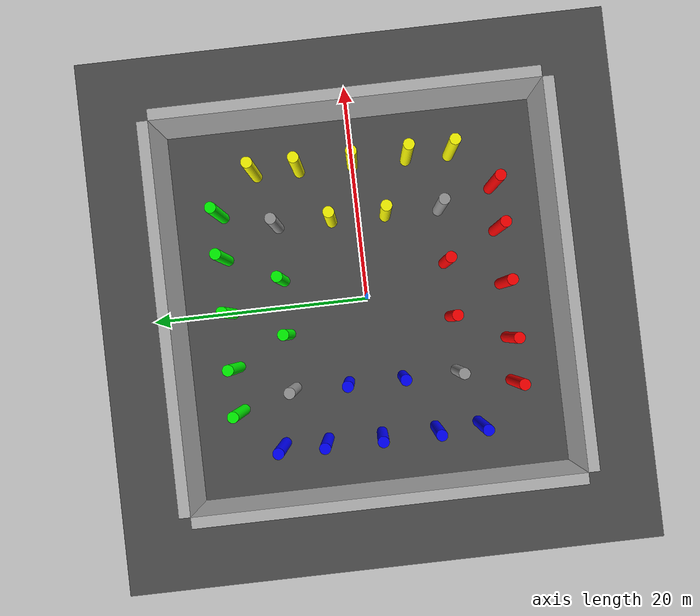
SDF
<sdf version="1.7">
 <world name="default">
  <include><uri>model://sun</uri></include>
  <include><uri>model://ground_plane</uri></include>
  <physics name="default_physics" default="0" type="ode">
   <ode>
    <solver>
     <type>quick</type>
     <iters>10</iters>
     <sor>1.3</sor>
     <use_dynamic_moi_rescaling>0</use_dynamic_moi_rescaling>
    </solver>
    <constraints>
     <cfm>0</cfm>
     <erp>0.2</erp>
     <contact_max_correcting_vel>100</contact_max_correcting_vel>
     <contact_surface_layer>0.001</contact_surface_layer>
    </constraints>
   </ode>
   <max_step_size>0.004</max_step_size>
   <real_time_factor>1</real_time_factor>
   <real_time_update_rate>250</real_time_update_rate>
  </physics>
  <gravity>0 0 -9.8066</gravity>
  <magnetic_field>6e-06 2.3e-05 -4.2e-05</magnetic_field>
  <atmosphere type="adiabatic"/>
  <scene><ambient>0.4 0.4 0.4 1</ambient><background>0.7 0.7 0.7 1</background><shadows>1</shadows></scene>
  <model name="asphalt_plane">
   <link name="link">
    <inertial>
     <mass>1</mass>
     <inertia><ixx>1</ixx><ixy>0</ixy><ixz>0</ixz><iyy>1</iyy><iyz>0</iyz><izz>1</izz></inertia>
    </inertial>
    <visual name="visual">
     <cast_shadows>0</cast_shadows>
     <geometry><box><size>50 50 0.1</size></box></geometry>
     <material>
      <script>
       <uri>model://asphalt_plane/materials/scripts</uri>
       <uri>model://asphalt_plane/materials/textures</uri>
       <name>vrc/asphalt</name>
      </script>
      <shader type="pixel"><normal_map>__default__</normal_map></shader>
      <ambient>0.5 0.5 0.5 1</ambient>
      <diffuse>0.5 0.5 0.5 1</diffuse>
      <specular>0.2 0.2 0.2 1</specular>
      <emissive>0 0 0 1</emissive>
     </material>
    </visual>
    <collision name="collision">
     <geometry><box><size>50 50 0.1</size></box></geometry>
     <surface>
      <friction>
       <ode><mu>1</mu><mu2>1</mu2><fdir1>0 0 0</fdir1><slip1>0</slip1><slip2>0</slip2></ode>
       <torsional>
        <coefficient>1</coefficient>
        <patch_radius>0</patch_radius>
        <surface_radius>0</surface_radius>
        <use_patch_radius>1</use_patch_radius>
        <ode><slip>0</slip></ode>
       </torsional>
      </friction>
      <bounce><restitution_coefficient>0</restitution_coefficient><threshold>1e+06</threshold></bounce>
      <contact>
       <collide_without_contact>0</collide_without_contact>
       <collide_without_contact_bitmask>1</collide_without_contact_bitmask>
       <collide_bitmask>1</collide_bitmask>
       <ode>
        <soft_cfm>0</soft_cfm>
        <soft_erp>0.2</soft_erp>
        <kp>1e+13</kp>
        <kd>1</kd>
        <max_vel>0.01</max_vel>
        <min_depth>0</min_depth>
       </ode>
       <bullet>
        <split_impulse>1</split_impulse>
        <split_impulse_penetration_threshold>-0.01</split_impulse_penetration_threshold>
        <soft_cfm>0</soft_cfm>
        <soft_erp>0.2</soft_erp>
        <kp>1e+13</kp>
        <kd>1</kd>
       </bullet>
      </contact>
     </surface>
    </collision>
   </link>
   <static>1</static>
   <pose>-0.063761 -0.010768 0 0 -0 0</pose>
  </model>
  <model name="red_cylinder">
   <link name="link">
    <inertial>
     <mass>1</mass>
     <inertia><ixx>0.145833</ixx><ixy>0</ixy><ixz>0</ixz><iyy>0.145833</iyy><iyz>0</iyz><izz>0.125</izz></inertia>
    </inertial>
    <visual name="visual">
     <geometry><cylinder><radius>0.5</radius><length>10</length></cylinder></geometry>
     <material>
      <script><name>Gazebo/Grey</name><uri>file://media/materials/scripts/gazebo.material</uri></script>
      <shader type="pixel"><normal_map>__default__</normal_map></shader>
      <ambient>1 0 0 0</ambient>
      <diffuse>0.7 0.7 0.7 1</diffuse>
      <specular>0.01 0.01 0.01 1</specular>
      <emissive>0 0 0 1</emissive>
     </material>
    </visual>
    <collision name="collision">
     <geometry><cylinder><radius>0.5</radius><length>10</length></cylinder></geometry>
     <surface>
      <friction>
       <ode><mu>1</mu><mu2>1</mu2><fdir1>0 0 0</fdir1><slip1>0</slip1><slip2>0</slip2></ode>
       <torsional>
        <coefficient>1</coefficient>
        <patch_radius>0</patch_radius>
        <surface_radius>0</surface_radius>
        <use_patch_radius>1</use_patch_radius>
        <ode><slip>0</slip></ode>
       </torsional>
      </friction>
      <bounce><restitution_coefficient>0</restitution_coefficient><threshold>1e+06</threshold></bounce>
      <contact>
       <collide_without_contact>0</collide_without_contact>
       <collide_without_contact_bitmask>1</collide_without_contact_bitmask>
       <collide_bitmask>1</collide_bitmask>
       <ode>
        <soft_cfm>0</soft_cfm>
        <soft_erp>0.2</soft_erp>
        <kp>1e+13</kp>
        <kd>1</kd>
        <max_vel>0.01</max_vel>
        <min_depth>0</min_depth>
       </ode>
       <bullet>
        <split_impulse>1</split_impulse>
        <split_impulse_penetration_threshold>-0.01</split_impulse_penetration_threshold>
        <soft_cfm>0</soft_cfm>
        <soft_erp>0.2</soft_erp>
        <kp>1e+13</kp>
        <kd>1</kd>
       </bullet>
      </contact>
     </surface>
    </collision>
   </link>
   <static>1</static>
   <pose>0.0144 -12.5 5 0 -0 0</pose>
  </model>
  <model name="yellow_cylinder">
   <link name="link">
    <inertial>
     <mass>1</mass>
     <inertia><ixx>0.145833</ixx><ixy>0</ixy><ixz>0</ixz><iyy>0.145833</iyy><iyz>0</iyz><izz>0.125</izz></inertia>
    </inertial>
    <visual name="visual">
     <geometry><cylinder><radius>0.5</radius><length>10</length></cylinder></geometry>
     <material>
      <script><name>Gazebo/Grey</name><uri>file://media/materials/scripts/gazebo.material</uri></script>
      <shader type="pixel"><normal_map>__default__</normal_map></shader>
      <ambient>1 1 0 0</ambient>
      <diffuse>0.7 0.7 0.7 1</diffuse>
      <specular>0.01 0.01 0.01 1</specular>
      <emissive>0 0 0 1</emissive>
     </material>
    </visual>
    <collision name="collision">
     <geometry><cylinder><radius>0.5</radius><length>10</length></cylinder></geometry>
     <surface>
      <friction>
       <ode><mu>1</mu><mu2>1</mu2><fdir1>0 0 0</fdir1><slip1>0</slip1><slip2>0</slip2></ode>
       <torsional>
        <coefficient>1</coefficient>
        <patch_radius>0</patch_radius>
        <surface_radius>0</surface_radius>
        <use_patch_radius>1</use_patch_radius>
        <ode><slip>0</slip></ode>
       </torsional>
      </friction>
      <bounce><restitution_coefficient>0</restitution_coefficient><threshold>1e+06</threshold></bounce>
      <contact>
       <collide_without_contact>0</collide_without_contact>
       <collide_without_contact_bitmask>1</collide_without_contact_bitmask>
       <collide_bitmask>1</collide_bitmask>
       <ode>
        <soft_cfm>0</soft_cfm>
        <soft_erp>0.2</soft_erp>
        <kp>1e+13</kp>
        <kd>1</kd>
        <max_vel>0.01</max_vel>
        <min_depth>0</min_depth>
       </ode>
       <bullet>
        <split_impulse>1</split_impulse>
        <split_impulse_penetration_threshold>-0.01</split_impulse_penetration_threshold>
        <soft_cfm>0</soft_cfm>
        <soft_erp>0.2</soft_erp>
        <kp>1e+13</kp>
        <kd>1</kd>
       </bullet>
      </contact>
     </surface>
    </collision>
   </link>
   <static>1</static>
   <pose>12.5 0 5 0 -0 0</pose>
  </model>
  <model name="green_cylinder">
   <link name="link">
    <inertial>
     <mass>1</mass>
     <inertia><ixx>0.145833</ixx><ixy>0</ixy><ixz>0</ixz><iyy>0.145833</iyy><iyz>0</iyz><izz>0.125</izz></inertia>
    </inertial>
    <visual name="visual">
     <geometry><cylinder><radius>0.5</radius><length>10</length></cylinder></geometry>
     <material>
      <script><name>Gazebo/Grey</name><uri>file://media/materials/scripts/gazebo.material</uri></script>
      <shader type="pixel"><normal_map>__default__</normal_map></shader>
      <ambient>0 1 0 0</ambient>
      <diffuse>0.7 0.7 0.7 1</diffuse>
      <specular>0.01 0.01 0.01 1</specular>
      <emissive>0 0 0 1</emissive>
     </material>
    </visual>
    <collision name="collision">
     <geometry><cylinder><radius>0.5</radius><length>10</length></cylinder></geometry>
     <surface>
      <friction>
       <ode><mu>1</mu><mu2>1</mu2><fdir1>0 0 0</fdir1><slip1>0</slip1><slip2>0</slip2></ode>
       <torsional>
        <coefficient>1</coefficient>
        <patch_radius>0</patch_radius>
        <surface_radius>0</surface_radius>
        <use_patch_radius>1</use_patch_radius>
        <ode><slip>0</slip></ode>
       </torsional>
      </friction>
      <bounce><restitution_coefficient>0</restitution_coefficient><threshold>1e+06</threshold></bounce>
      <contact>
       <collide_without_contact>0</collide_without_contact>
       <collide_without_contact_bitmask>1</collide_without_contact_bitmask>
       <collide_bitmask>1</collide_bitmask>
       <ode>
        <soft_cfm>0</soft_cfm>
        <soft_erp>0.2</soft_erp>
        <kp>1e+13</kp>
        <kd>1</kd>
        <max_vel>0.01</max_vel>
        <min_depth>0</min_depth>
       </ode>
       <bullet>
        <split_impulse>1</split_impulse>
        <split_impulse_penetration_threshold>-0.01</split_impulse_penetration_threshold>
        <soft_cfm>0</soft_cfm>
        <soft_erp>0.2</soft_erp>
        <kp>1e+13</kp>
        <kd>1</kd>
       </bullet>
      </contact>
     </surface>
    </collision>
   </link>
   <static>1</static>
   <pose>0 12.5 5 0 -0 0</pose>
  </model>
  <model name="blue_cylinder">
   <link name="link">
    <inertial>
     <mass>1</mass>
     <inertia><ixx>0.145833</ixx><ixy>0</ixy><ixz>0</ixz><iyy>0.145833</iyy><iyz>0</iyz><izz>0.125</izz></inertia>
    </inertial>
    <visual name="visual">
     <geometry><cylinder><radius>0.5</radius><length>10</length></cylinder></geometry>
     <material>
      <script><name>Gazebo/Grey</name><uri>file://media/materials/scripts/gazebo.material</uri></script>
      <shader type="pixel"><normal_map>__default__</normal_map></shader>
      <ambient>0 0 1 0</ambient>
      <diffuse>0.7 0.7 0.7 1</diffuse>
      <specular>0.01 0.01 0.01 1</specular>
      <emissive>0 0 0 1</emissive>
     </material>
    </visual>
    <collision name="collision">
     <geometry><cylinder><radius>0.5</radius><length>10</length></cylinder></geometry>
     <surface>
      <friction>
       <ode><mu>1</mu><mu2>1</mu2><fdir1>0 0 0</fdir1><slip1>0</slip1><slip2>0</slip2></ode>
       <torsional>
        <coefficient>1</coefficient>
        <patch_radius>0</patch_radius>
        <surface_radius>0</surface_radius>
        <use_patch_radius>1</use_patch_radius>
        <ode><slip>0</slip></ode>
       </torsional>
      </friction>
      <bounce><restitution_coefficient>0</restitution_coefficient><threshold>1e+06</threshold></bounce>
      <contact>
       <collide_without_contact>0</collide_without_contact>
       <collide_without_contact_bitmask>1</collide_without_contact_bitmask>
       <collide_bitmask>1</collide_bitmask>
       <ode>
        <soft_cfm>0</soft_cfm>
        <soft_erp>0.2</soft_erp>
        <kp>1e+13</kp>
        <kd>1</kd>
        <max_vel>0.01</max_vel>
        <min_depth>0</min_depth>
       </ode>
       <bullet>
        <split_impulse>1</split_impulse>
        <split_impulse_penetration_threshold>-0.01</split_impulse_penetration_threshold>
        <soft_cfm>0</soft_cfm>
        <soft_erp>0.2</soft_erp>
        <kp>1e+13</kp>
        <kd>1</kd>
       </bullet>
      </contact>
     </surface>
    </collision>
   </link>
   <static>1</static>
   <pose>-12.5 0 5 0 -0 0</pose>
  </model>
  <model name="yellow_cylinder_clone">
   <link name="link">
    <inertial>
     <mass>1</mass>
     <inertia><ixx>0.145833</ixx><ixy>0</ixy><ixz>0</ixz><iyy>0.145833</iyy><iyz>0</iyz><izz>0.125</izz></inertia>
    </inertial>
    <visual name="visual">
     <geometry><cylinder><radius>0.5</radius><length>10</length></cylinder></geometry>
     <material>
      <script><name>Gazebo/Grey</name><uri>file://media/materials/scripts/gazebo.material</uri></script>
      <shader type="pixel"><normal_map>__default__</normal_map></shader>
      <ambient>1 1 0 0</ambient>
      <diffuse>0.7 0.7 0.7 1</diffuse>
      <specular>0.01 0.01 0.01 1</specular>
      <emissive>0 0 0 1</emissive>
     </material>
    </visual>
    <collision name="collision">
     <geometry><cylinder><radius>0.5</radius><length>10</length></cylinder></geometry>
     <surface>
      <friction>
       <ode><mu>1</mu><mu2>1</mu2><fdir1>0 0 0</fdir1><slip1>0</slip1><slip2>0</slip2></ode>
       <torsional>
        <coefficient>1</coefficient>
        <patch_radius>0</patch_radius>
        <surface_radius>0</surface_radius>
        <use_patch_radius>1</use_patch_radius>
        <ode><slip>0</slip></ode>
       </torsional>
      </friction>
      <bounce><restitution_coefficient>0</restitution_coefficient><threshold>1e+06</threshold></bounce>
      <contact>
       <collide_without_contact>0</collide_without_contact>
       <collide_without_contact_bitmask>1</collide_without_contact_bitmask>
       <collide_bitmask>1</collide_bitmask>
       <ode>
        <soft_cfm>0</soft_cfm>
        <soft_erp>0.2</soft_erp>
        <kp>1e+13</kp>
        <kd>1</kd>
        <max_vel>0.01</max_vel>
        <min_depth>0</min_depth>
       </ode>
       <bullet>
        <split_impulse>1</split_impulse>
        <split_impulse_penetration_threshold>-0.01</split_impulse_penetration_threshold>
        <soft_cfm>0</soft_cfm>
        <soft_erp>0.2</soft_erp>
        <kp>1e+13</kp>
        <kd>1</kd>
       </bullet>
      </contact>
     </surface>
    </collision>
   </link>
   <static>1</static>
   <pose>12.5 5 5 0 -0 0</pose>
  </model>
  <model name="yellow_cylinder_clone_clone">
   <link name="link">
    <inertial>
     <mass>1</mass>
     <inertia><ixx>0.145833</ixx><ixy>0</ixy><ixz>0</ixz><iyy>0.145833</iyy><iyz>0</iyz><izz>0.125</izz></inertia>
    </inertial>
    <visual name="visual">
     <geometry><cylinder><radius>0.5</radius><length>10</length></cylinder></geometry>
     <material>
      <script><name>Gazebo/Grey</name><uri>file://media/materials/scripts/gazebo.material</uri></script>
      <shader type="pixel"><normal_map>__default__</normal_map></shader>
      <ambient>1 1 0 0</ambient>
      <diffuse>0.7 0.7 0.7 1</diffuse>
      <specular>0.01 0.01 0.01 1</specular>
      <emissive>0 0 0 1</emissive>
     </material>
    </visual>
    <collision name="collision">
     <geometry><cylinder><radius>0.5</radius><length>10</length></cylinder></geometry>
     <surface>
      <friction>
       <ode><mu>1</mu><mu2>1</mu2><fdir1>0 0 0</fdir1><slip1>0</slip1><slip2>0</slip2></ode>
       <torsional>
        <coefficient>1</coefficient>
        <patch_radius>0</patch_radius>
        <surface_radius>0</surface_radius>
        <use_patch_radius>1</use_patch_radius>
        <ode><slip>0</slip></ode>
       </torsional>
      </friction>
      <bounce><restitution_coefficient>0</restitution_coefficient><threshold>1e+06</threshold></bounce>
      <contact>
       <collide_without_contact>0</collide_without_contact>
       <collide_without_contact_bitmask>1</collide_without_contact_bitmask>
       <collide_bitmask>1</collide_bitmask>
       <ode>
        <soft_cfm>0</soft_cfm>
        <soft_erp>0.2</soft_erp>
        <kp>1e+13</kp>
        <kd>1</kd>
        <max_vel>0.01</max_vel>
        <min_depth>0</min_depth>
       </ode>
       <bullet>
        <split_impulse>1</split_impulse>
        <split_impulse_penetration_threshold>-0.01</split_impulse_penetration_threshold>
        <soft_cfm>0</soft_cfm>
        <soft_erp>0.2</soft_erp>
        <kp>1e+13</kp>
        <kd>1</kd>
       </bullet>
      </contact>
     </surface>
    </collision>
   </link>
   <static>1</static>
   <pose>12.5 9 5 0 -0 0</pose>
  </model>
  <model name="yellow_cylinder_clone_0">
   <link name="link">
    <inertial>
     <mass>1</mass>
     <inertia><ixx>0.145833</ixx><ixy>0</ixy><ixz>0</ixz><iyy>0.145833</iyy><iyz>0</iyz><izz>0.125</izz></inertia>
    </inertial>
    <visual name="visual">
     <geometry><cylinder><radius>0.5</radius><length>10</length></cylinder></geometry>
     <material>
      <script><name>Gazebo/Grey</name><uri>file://media/materials/scripts/gazebo.material</uri></script>
      <shader type="pixel"><normal_map>__default__</normal_map></shader>
      <ambient>1 1 0 0</ambient>
      <diffuse>0.7 0.7 0.7 1</diffuse>
      <specular>0.01 0.01 0.01 1</specular>
      <emissive>0 0 0 1</emissive>
     </material>
    </visual>
    <collision name="collision">
     <geometry><cylinder><radius>0.5</radius><length>10</length></cylinder></geometry>
     <surface>
      <friction>
       <ode><mu>1</mu><mu2>1</mu2><fdir1>0 0 0</fdir1><slip1>0</slip1><slip2>0</slip2></ode>
       <torsional>
        <coefficient>1</coefficient>
        <patch_radius>0</patch_radius>
        <surface_radius>0</surface_radius>
        <use_patch_radius>1</use_patch_radius>
        <ode><slip>0</slip></ode>
       </torsional>
      </friction>
      <bounce><restitution_coefficient>0</restitution_coefficient><threshold>1e+06</threshold></bounce>
      <contact>
       <collide_without_contact>0</collide_without_contact>
       <collide_without_contact_bitmask>1</collide_without_contact_bitmask>
       <collide_bitmask>1</collide_bitmask>
       <ode>
        <soft_cfm>0</soft_cfm>
        <soft_erp>0.2</soft_erp>
        <kp>1e+13</kp>
        <kd>1</kd>
        <max_vel>0.01</max_vel>
        <min_depth>0</min_depth>
       </ode>
       <bullet>
        <split_impulse>1</split_impulse>
        <split_impulse_penetration_threshold>-0.01</split_impulse_penetration_threshold>
        <soft_cfm>0</soft_cfm>
        <soft_erp>0.2</soft_erp>
        <kp>1e+13</kp>
        <kd>1</kd>
       </bullet>
      </contact>
     </surface>
    </collision>
   </link>
   <static>1</static>
   <pose>12.5 -5 5 0 -0 0</pose>
  </model>
  <model name="yellow_cylinder_clone_1">
   <link name="link">
    <inertial>
     <mass>1</mass>
     <inertia><ixx>0.145833</ixx><ixy>0</ixy><ixz>0</ixz><iyy>0.145833</iyy><iyz>0</iyz><izz>0.125</izz></inertia>
    </inertial>
    <visual name="visual">
     <geometry><cylinder><radius>0.5</radius><length>10</length></cylinder></geometry>
     <material>
      <script><name>Gazebo/Grey</name><uri>file://media/materials/scripts/gazebo.material</uri></script>
      <shader type="pixel"><normal_map>__default__</normal_map></shader>
      <ambient>1 1 0 0</ambient>
      <diffuse>0.7 0.7 0.7 1</diffuse>
      <specular>0.01 0.01 0.01 1</specular>
      <emissive>0 0 0 1</emissive>
     </material>
    </visual>
    <collision name="collision">
     <geometry><cylinder><radius>0.5</radius><length>10</length></cylinder></geometry>
     <surface>
      <friction>
       <ode><mu>1</mu><mu2>1</mu2><fdir1>0 0 0</fdir1><slip1>0</slip1><slip2>0</slip2></ode>
       <torsional>
        <coefficient>1</coefficient>
        <patch_radius>0</patch_radius>
        <surface_radius>0</surface_radius>
        <use_patch_radius>1</use_patch_radius>
        <ode><slip>0</slip></ode>
       </torsional>
      </friction>
      <bounce><restitution_coefficient>0</restitution_coefficient><threshold>1e+06</threshold></bounce>
      <contact>
       <collide_without_contact>0</collide_without_contact>
       <collide_without_contact_bitmask>1</collide_without_contact_bitmask>
       <collide_bitmask>1</collide_bitmask>
       <ode>
        <soft_cfm>0</soft_cfm>
        <soft_erp>0.2</soft_erp>
        <kp>1e+13</kp>
        <kd>1</kd>
        <max_vel>0.01</max_vel>
        <min_depth>0</min_depth>
       </ode>
       <bullet>
        <split_impulse>1</split_impulse>
        <split_impulse_penetration_threshold>-0.01</split_impulse_penetration_threshold>
        <soft_cfm>0</soft_cfm>
        <soft_erp>0.2</soft_erp>
        <kp>1e+13</kp>
        <kd>1</kd>
       </bullet>
      </contact>
     </surface>
    </collision>
   </link>
   <static>1</static>
   <pose>12.5 -9 5 0 -0 0</pose>
  </model>
  <model name="red_cylinder_clone">
   <link name="link">
    <inertial>
     <mass>1</mass>
     <inertia><ixx>0.145833</ixx><ixy>0</ixy><ixz>0</ixz><iyy>0.145833</iyy><iyz>0</iyz><izz>0.125</izz></inertia>
    </inertial>
    <visual name="visual">
     <geometry><cylinder><radius>0.5</radius><length>10</length></cylinder></geometry>
     <material>
      <script><name>Gazebo/Grey</name><uri>file://media/materials/scripts/gazebo.material</uri></script>
      <shader type="pixel"><normal_map>__default__</normal_map></shader>
      <ambient>1 0 0 0</ambient>
      <diffuse>0.7 0.7 0.7 1</diffuse>
      <specular>0.01 0.01 0.01 1</specular>
      <emissive>0 0 0 1</emissive>
     </material>
    </visual>
    <collision name="collision">
     <geometry><cylinder><radius>0.5</radius><length>10</length></cylinder></geometry>
     <surface>
      <friction>
       <ode><mu>1</mu><mu2>1</mu2><fdir1>0 0 0</fdir1><slip1>0</slip1><slip2>0</slip2></ode>
       <torsional>
        <coefficient>1</coefficient>
        <patch_radius>0</patch_radius>
        <surface_radius>0</surface_radius>
        <use_patch_radius>1</use_patch_radius>
        <ode><slip>0</slip></ode>
       </torsional>
      </friction>
      <bounce><restitution_coefficient>0</restitution_coefficient><threshold>1e+06</threshold></bounce>
      <contact>
       <collide_without_contact>0</collide_without_contact>
       <collide_without_contact_bitmask>1</collide_without_contact_bitmask>
       <collide_bitmask>1</collide_bitmask>
       <ode>
        <soft_cfm>0</soft_cfm>
        <soft_erp>0.2</soft_erp>
        <kp>1e+13</kp>
        <kd>1</kd>
        <max_vel>0.01</max_vel>
        <min_depth>0</min_depth>
       </ode>
       <bullet>
        <split_impulse>1</split_impulse>
        <split_impulse_penetration_threshold>-0.01</split_impulse_penetration_threshold>
        <soft_cfm>0</soft_cfm>
        <soft_erp>0.2</soft_erp>
        <kp>1e+13</kp>
        <kd>1</kd>
       </bullet>
      </contact>
     </surface>
    </collision>
   </link>
   <static>1</static>
   <pose>-5 -12.5 5 0 -0 0</pose>
  </model>
  <model name="red_cylinder_clone_0">
   <link name="link">
    <inertial>
     <mass>1</mass>
     <inertia><ixx>0.145833</ixx><ixy>0</ixy><ixz>0</ixz><iyy>0.145833</iyy><iyz>0</iyz><izz>0.125</izz></inertia>
    </inertial>
    <visual name="visual">
     <geometry><cylinder><radius>0.5</radius><length>10</length></cylinder></geometry>
     <material>
      <script><name>Gazebo/Grey</name><uri>file://media/materials/scripts/gazebo.material</uri></script>
      <shader type="pixel"><normal_map>__default__</normal_map></shader>
      <ambient>1 0 0 0</ambient>
      <diffuse>0.7 0.7 0.7 1</diffuse>
      <specular>0.01 0.01 0.01 1</specular>
      <emissive>0 0 0 1</emissive>
     </material>
    </visual>
    <collision name="collision">
     <geometry><cylinder><radius>0.5</radius><length>10</length></cylinder></geometry>
     <surface>
      <friction>
       <ode><mu>1</mu><mu2>1</mu2><fdir1>0 0 0</fdir1><slip1>0</slip1><slip2>0</slip2></ode>
       <torsional>
        <coefficient>1</coefficient>
        <patch_radius>0</patch_radius>
        <surface_radius>0</surface_radius>
        <use_patch_radius>1</use_patch_radius>
        <ode><slip>0</slip></ode>
       </torsional>
      </friction>
      <bounce><restitution_coefficient>0</restitution_coefficient><threshold>1e+06</threshold></bounce>
      <contact>
       <collide_without_contact>0</collide_without_contact>
       <collide_without_contact_bitmask>1</collide_without_contact_bitmask>
       <collide_bitmask>1</collide_bitmask>
       <ode>
        <soft_cfm>0</soft_cfm>
        <soft_erp>0.2</soft_erp>
        <kp>1e+13</kp>
        <kd>1</kd>
        <max_vel>0.01</max_vel>
        <min_depth>0</min_depth>
       </ode>
       <bullet>
        <split_impulse>1</split_impulse>
        <split_impulse_penetration_threshold>-0.01</split_impulse_penetration_threshold>
        <soft_cfm>0</soft_cfm>
        <soft_erp>0.2</soft_erp>
        <kp>1e+13</kp>
        <kd>1</kd>
       </bullet>
      </contact>
     </surface>
    </collision>
   </link>
   <static>1</static>
   <pose>5 -12.5 5 0 -0 0</pose>
  </model>
  <model name="red_cylinder_clone_1">
   <link name="link">
    <inertial>
     <mass>1</mass>
     <inertia><ixx>0.145833</ixx><ixy>0</ixy><ixz>0</ixz><iyy>0.145833</iyy><iyz>0</iyz><izz>0.125</izz></inertia>
    </inertial>
    <visual name="visual">
     <geometry><cylinder><radius>0.5</radius><length>10</length></cylinder></geometry>
     <material>
      <script><name>Gazebo/Grey</name><uri>file://media/materials/scripts/gazebo.material</uri></script>
      <shader type="pixel"><normal_map>__default__</normal_map></shader>
      <ambient>1 0 0 0</ambient>
      <diffuse>0.7 0.7 0.7 1</diffuse>
      <specular>0.01 0.01 0.01 1</specular>
      <emissive>0 0 0 1</emissive>
     </material>
    </visual>
    <collision name="collision">
     <geometry><cylinder><radius>0.5</radius><length>10</length></cylinder></geometry>
     <surface>
      <friction>
       <ode><mu>1</mu><mu2>1</mu2><fdir1>0 0 0</fdir1><slip1>0</slip1><slip2>0</slip2></ode>
       <torsional>
        <coefficient>1</coefficient>
        <patch_radius>0</patch_radius>
        <surface_radius>0</surface_radius>
        <use_patch_radius>1</use_patch_radius>
        <ode><slip>0</slip></ode>
       </torsional>
      </friction>
      <bounce><restitution_coefficient>0</restitution_coefficient><threshold>1e+06</threshold></bounce>
      <contact>
       <collide_without_contact>0</collide_without_contact>
       <collide_without_contact_bitmask>1</collide_without_contact_bitmask>
       <collide_bitmask>1</collide_bitmask>
       <ode>
        <soft_cfm>0</soft_cfm>
        <soft_erp>0.2</soft_erp>
        <kp>1e+13</kp>
        <kd>1</kd>
        <max_vel>0.01</max_vel>
        <min_depth>0</min_depth>
       </ode>
       <bullet>
        <split_impulse>1</split_impulse>
        <split_impulse_penetration_threshold>-0.01</split_impulse_penetration_threshold>
        <soft_cfm>0</soft_cfm>
        <soft_erp>0.2</soft_erp>
        <kp>1e+13</kp>
        <kd>1</kd>
       </bullet>
      </contact>
     </surface>
    </collision>
   </link>
   <static>1</static>
   <pose>-9 -12.5 5 0 -0 0</pose>
  </model>
  <model name="red_cylinder_clone_2">
   <link name="link">
    <inertial>
     <mass>1</mass>
     <inertia><ixx>0.145833</ixx><ixy>0</ixy><ixz>0</ixz><iyy>0.145833</iyy><iyz>0</iyz><izz>0.125</izz></inertia>
    </inertial>
    <visual name="visual">
     <geometry><cylinder><radius>0.5</radius><length>10</length></cylinder></geometry>
     <material>
      <script><name>Gazebo/Grey</name><uri>file://media/materials/scripts/gazebo.material</uri></script>
      <shader type="pixel"><normal_map>__default__</normal_map></shader>
      <ambient>1 0 0 0</ambient>
      <diffuse>0.7 0.7 0.7 1</diffuse>
      <specular>0.01 0.01 0.01 1</specular>
      <emissive>0 0 0 1</emissive>
     </material>
    </visual>
    <collision name="collision">
     <geometry><cylinder><radius>0.5</radius><length>10</length></cylinder></geometry>
     <surface>
      <friction>
       <ode><mu>1</mu><mu2>1</mu2><fdir1>0 0 0</fdir1><slip1>0</slip1><slip2>0</slip2></ode>
       <torsional>
        <coefficient>1</coefficient>
        <patch_radius>0</patch_radius>
        <surface_radius>0</surface_radius>
        <use_patch_radius>1</use_patch_radius>
        <ode><slip>0</slip></ode>
       </torsional>
      </friction>
      <bounce><restitution_coefficient>0</restitution_coefficient><threshold>1e+06</threshold></bounce>
      <contact>
       <collide_without_contact>0</collide_without_contact>
       <collide_without_contact_bitmask>1</collide_without_contact_bitmask>
       <collide_bitmask>1</collide_bitmask>
       <ode>
        <soft_cfm>0</soft_cfm>
        <soft_erp>0.2</soft_erp>
        <kp>1e+13</kp>
        <kd>1</kd>
        <max_vel>0.01</max_vel>
        <min_depth>0</min_depth>
       </ode>
       <bullet>
        <split_impulse>1</split_impulse>
        <split_impulse_penetration_threshold>-0.01</split_impulse_penetration_threshold>
        <soft_cfm>0</soft_cfm>
        <soft_erp>0.2</soft_erp>
        <kp>1e+13</kp>
        <kd>1</kd>
       </bullet>
      </contact>
     </surface>
    </collision>
   </link>
   <static>1</static>
   <pose>9 -12.5 5 0 -0 0</pose>
  </model>
  <model name="blue_cylinder_clone">
   <link name="link">
    <inertial>
     <mass>1</mass>
     <inertia><ixx>0.145833</ixx><ixy>0</ixy><ixz>0</ixz><iyy>0.145833</iyy><iyz>0</iyz><izz>0.125</izz></inertia>
    </inertial>
    <visual name="visual">
     <geometry><cylinder><radius>0.5</radius><length>10</length></cylinder></geometry>
     <material>
      <script><name>Gazebo/Grey</name><uri>file://media/materials/scripts/gazebo.material</uri></script>
      <shader type="pixel"><normal_map>__default__</normal_map></shader>
      <ambient>0 0 1 0</ambient>
      <diffuse>0.7 0.7 0.7 1</diffuse>
      <specular>0.01 0.01 0.01 1</specular>
      <emissive>0 0 0 1</emissive>
     </material>
    </visual>
    <collision name="collision">
     <geometry><cylinder><radius>0.5</radius><length>10</length></cylinder></geometry>
     <surface>
      <friction>
       <ode><mu>1</mu><mu2>1</mu2><fdir1>0 0 0</fdir1><slip1>0</slip1><slip2>0</slip2></ode>
       <torsional>
        <coefficient>1</coefficient>
        <patch_radius>0</patch_radius>
        <surface_radius>0</surface_radius>
        <use_patch_radius>1</use_patch_radius>
        <ode><slip>0</slip></ode>
       </torsional>
      </friction>
      <bounce><restitution_coefficient>0</restitution_coefficient><threshold>1e+06</threshold></bounce>
      <contact>
       <collide_without_contact>0</collide_without_contact>
       <collide_without_contact_bitmask>1</collide_without_contact_bitmask>
       <collide_bitmask>1</collide_bitmask>
       <ode>
        <soft_cfm>0</soft_cfm>
        <soft_erp>0.2</soft_erp>
        <kp>1e+13</kp>
        <kd>1</kd>
        <max_vel>0.01</max_vel>
        <min_depth>0</min_depth>
       </ode>
       <bullet>
        <split_impulse>1</split_impulse>
        <split_impulse_penetration_threshold>-0.01</split_impulse_penetration_threshold>
        <soft_cfm>0</soft_cfm>
        <soft_erp>0.2</soft_erp>
        <kp>1e+13</kp>
        <kd>1</kd>
       </bullet>
      </contact>
     </surface>
    </collision>
   </link>
   <static>1</static>
   <pose>-12.5 -5 5 0 -0 0</pose>
  </model>
  <model name="blue_cylinder_clone_0">
   <link name="link">
    <inertial>
     <mass>1</mass>
     <inertia><ixx>0.145833</ixx><ixy>0</ixy><ixz>0</ixz><iyy>0.145833</iyy><iyz>0</iyz><izz>0.125</izz></inertia>
    </inertial>
    <visual name="visual">
     <geometry><cylinder><radius>0.5</radius><length>10</length></cylinder></geometry>
     <material>
      <script><name>Gazebo/Grey</name><uri>file://media/materials/scripts/gazebo.material</uri></script>
      <shader type="pixel"><normal_map>__default__</normal_map></shader>
      <ambient>0 0 1 0</ambient>
      <diffuse>0.7 0.7 0.7 1</diffuse>
      <specular>0.01 0.01 0.01 1</specular>
      <emissive>0 0 0 1</emissive>
     </material>
    </visual>
    <collision name="collision">
     <geometry><cylinder><radius>0.5</radius><length>10</length></cylinder></geometry>
     <surface>
      <friction>
       <ode><mu>1</mu><mu2>1</mu2><fdir1>0 0 0</fdir1><slip1>0</slip1><slip2>0</slip2></ode>
       <torsional>
        <coefficient>1</coefficient>
        <patch_radius>0</patch_radius>
        <surface_radius>0</surface_radius>
        <use_patch_radius>1</use_patch_radius>
        <ode><slip>0</slip></ode>
       </torsional>
      </friction>
      <bounce><restitution_coefficient>0</restitution_coefficient><threshold>1e+06</threshold></bounce>
      <contact>
       <collide_without_contact>0</collide_without_contact>
       <collide_without_contact_bitmask>1</collide_without_contact_bitmask>
       <collide_bitmask>1</collide_bitmask>
       <ode>
        <soft_cfm>0</soft_cfm>
        <soft_erp>0.2</soft_erp>
        <kp>1e+13</kp>
        <kd>1</kd>
        <max_vel>0.01</max_vel>
        <min_depth>0</min_depth>
       </ode>
       <bullet>
        <split_impulse>1</split_impulse>
        <split_impulse_penetration_threshold>-0.01</split_impulse_penetration_threshold>
        <soft_cfm>0</soft_cfm>
        <soft_erp>0.2</soft_erp>
        <kp>1e+13</kp>
        <kd>1</kd>
       </bullet>
      </contact>
     </surface>
    </collision>
   </link>
   <static>1</static>
   <pose>-12.5 5 5 0 -0 0</pose>
  </model>
  <model name="blue_cylinder_clone_1">
   <link name="link">
    <inertial>
     <mass>1</mass>
     <inertia><ixx>0.145833</ixx><ixy>0</ixy><ixz>0</ixz><iyy>0.145833</iyy><iyz>0</iyz><izz>0.125</izz></inertia>
    </inertial>
    <visual name="visual">
     <geometry><cylinder><radius>0.5</radius><length>10</length></cylinder></geometry>
     <material>
      <script><name>Gazebo/Grey</name><uri>file://media/materials/scripts/gazebo.material</uri></script>
      <shader type="pixel"><normal_map>__default__</normal_map></shader>
      <ambient>0 0 1 0</ambient>
      <diffuse>0.7 0.7 0.7 1</diffuse>
      <specular>0.01 0.01 0.01 1</specular>
      <emissive>0 0 0 1</emissive>
     </material>
    </visual>
    <collision name="collision">
     <geometry><cylinder><radius>0.5</radius><length>10</length></cylinder></geometry>
     <surface>
      <friction>
       <ode><mu>1</mu><mu2>1</mu2><fdir1>0 0 0</fdir1><slip1>0</slip1><slip2>0</slip2></ode>
       <torsional>
        <coefficient>1</coefficient>
        <patch_radius>0</patch_radius>
        <surface_radius>0</surface_radius>
        <use_patch_radius>1</use_patch_radius>
        <ode><slip>0</slip></ode>
       </torsional>
      </friction>
      <bounce><restitution_coefficient>0</restitution_coefficient><threshold>1e+06</threshold></bounce>
      <contact>
       <collide_without_contact>0</collide_without_contact>
       <collide_without_contact_bitmask>1</collide_without_contact_bitmask>
       <collide_bitmask>1</collide_bitmask>
       <ode>
        <soft_cfm>0</soft_cfm>
        <soft_erp>0.2</soft_erp>
        <kp>1e+13</kp>
        <kd>1</kd>
        <max_vel>0.01</max_vel>
        <min_depth>0</min_depth>
       </ode>
       <bullet>
        <split_impulse>1</split_impulse>
        <split_impulse_penetration_threshold>-0.01</split_impulse_penetration_threshold>
        <soft_cfm>0</soft_cfm>
        <soft_erp>0.2</soft_erp>
        <kp>1e+13</kp>
        <kd>1</kd>
       </bullet>
      </contact>
     </surface>
    </collision>
   </link>
   <static>1</static>
   <pose>-12.5 9 5 0 -0 0</pose>
  </model>
  <model name="blue_cylinder_clone_2">
   <link name="link">
    <inertial>
     <mass>1</mass>
     <inertia><ixx>0.145833</ixx><ixy>0</ixy><ixz>0</ixz><iyy>0.145833</iyy><iyz>0</iyz><izz>0.125</izz></inertia>
    </inertial>
    <visual name="visual">
     <geometry><cylinder><radius>0.5</radius><length>10</length></cylinder></geometry>
     <material>
      <script><name>Gazebo/Grey</name><uri>file://media/materials/scripts/gazebo.material</uri></script>
      <shader type="pixel"><normal_map>__default__</normal_map></shader>
      <ambient>0 0 1 0</ambient>
      <diffuse>0.7 0.7 0.7 1</diffuse>
      <specular>0.01 0.01 0.01 1</specular>
      <emissive>0 0 0 1</emissive>
     </material>
    </visual>
    <collision name="collision">
     <geometry><cylinder><radius>0.5</radius><length>10</length></cylinder></geometry>
     <surface>
      <friction>
       <ode><mu>1</mu><mu2>1</mu2><fdir1>0 0 0</fdir1><slip1>0</slip1><slip2>0</slip2></ode>
       <torsional>
        <coefficient>1</coefficient>
        <patch_radius>0</patch_radius>
        <surface_radius>0</surface_radius>
        <use_patch_radius>1</use_patch_radius>
        <ode><slip>0</slip></ode>
       </torsional>
      </friction>
      <bounce><restitution_coefficient>0</restitution_coefficient><threshold>1e+06</threshold></bounce>
      <contact>
       <collide_without_contact>0</collide_without_contact>
       <collide_without_contact_bitmask>1</collide_without_contact_bitmask>
       <collide_bitmask>1</collide_bitmask>
       <ode>
        <soft_cfm>0</soft_cfm>
        <soft_erp>0.2</soft_erp>
        <kp>1e+13</kp>
        <kd>1</kd>
        <max_vel>0.01</max_vel>
        <min_depth>0</min_depth>
       </ode>
       <bullet>
        <split_impulse>1</split_impulse>
        <split_impulse_penetration_threshold>-0.01</split_impulse_penetration_threshold>
        <soft_cfm>0</soft_cfm>
        <soft_erp>0.2</soft_erp>
        <kp>1e+13</kp>
        <kd>1</kd>
       </bullet>
      </contact>
     </surface>
    </collision>
   </link>
   <static>1</static>
   <pose>-12.5 -9 5 0 -0 0</pose>
  </model>
  <model name="green_cylinder_clone">
   <link name="link">
    <inertial>
     <mass>1</mass>
     <inertia><ixx>0.145833</ixx><ixy>0</ixy><ixz>0</ixz><iyy>0.145833</iyy><iyz>0</iyz><izz>0.125</izz></inertia>
    </inertial>
    <visual name="visual">
     <geometry><cylinder><radius>0.5</radius><length>10</length></cylinder></geometry>
     <material>
      <script><name>Gazebo/Grey</name><uri>file://media/materials/scripts/gazebo.material</uri></script>
      <shader type="pixel"><normal_map>__default__</normal_map></shader>
      <ambient>0 1 0 0</ambient>
      <diffuse>0.7 0.7 0.7 1</diffuse>
      <specular>0.01 0.01 0.01 1</specular>
      <emissive>0 0 0 1</emissive>
     </material>
    </visual>
    <collision name="collision">
     <geometry><cylinder><radius>0.5</radius><length>10</length></cylinder></geometry>
     <surface>
      <friction>
       <ode><mu>1</mu><mu2>1</mu2><fdir1>0 0 0</fdir1><slip1>0</slip1><slip2>0</slip2></ode>
       <torsional>
        <coefficient>1</coefficient>
        <patch_radius>0</patch_radius>
        <surface_radius>0</surface_radius>
        <use_patch_radius>1</use_patch_radius>
        <ode><slip>0</slip></ode>
       </torsional>
      </friction>
      <bounce><restitution_coefficient>0</restitution_coefficient><threshold>1e+06</threshold></bounce>
      <contact>
       <collide_without_contact>0</collide_without_contact>
       <collide_without_contact_bitmask>1</collide_without_contact_bitmask>
       <collide_bitmask>1</collide_bitmask>
       <ode>
        <soft_cfm>0</soft_cfm>
        <soft_erp>0.2</soft_erp>
        <kp>1e+13</kp>
        <kd>1</kd>
        <max_vel>0.01</max_vel>
        <min_depth>0</min_depth>
       </ode>
       <bullet>
        <split_impulse>1</split_impulse>
        <split_impulse_penetration_threshold>-0.01</split_impulse_penetration_threshold>
        <soft_cfm>0</soft_cfm>
        <soft_erp>0.2</soft_erp>
        <kp>1e+13</kp>
        <kd>1</kd>
       </bullet>
      </contact>
     </surface>
    </collision>
   </link>
   <static>1</static>
   <pose>-5 12.5 5 0 -0 0</pose>
  </model>
  <model name="green_cylinder_clone_0">
   <link name="link">
    <inertial>
     <mass>1</mass>
     <inertia><ixx>0.145833</ixx><ixy>0</ixy><ixz>0</ixz><iyy>0.145833</iyy><iyz>0</iyz><izz>0.125</izz></inertia>
    </inertial>
    <visual name="visual">
     <geometry><cylinder><radius>0.5</radius><length>10</length></cylinder></geometry>
     <material>
      <script><name>Gazebo/Grey</name><uri>file://media/materials/scripts/gazebo.material</uri></script>
      <shader type="pixel"><normal_map>__default__</normal_map></shader>
      <ambient>0 1 0 0</ambient>
      <diffuse>0.7 0.7 0.7 1</diffuse>
      <specular>0.01 0.01 0.01 1</specular>
      <emissive>0 0 0 1</emissive>
     </material>
    </visual>
    <collision name="collision">
     <geometry><cylinder><radius>0.5</radius><length>10</length></cylinder></geometry>
     <surface>
      <friction>
       <ode><mu>1</mu><mu2>1</mu2><fdir1>0 0 0</fdir1><slip1>0</slip1><slip2>0</slip2></ode>
       <torsional>
        <coefficient>1</coefficient>
        <patch_radius>0</patch_radius>
        <surface_radius>0</surface_radius>
        <use_patch_radius>1</use_patch_radius>
        <ode><slip>0</slip></ode>
       </torsional>
      </friction>
      <bounce><restitution_coefficient>0</restitution_coefficient><threshold>1e+06</threshold></bounce>
      <contact>
       <collide_without_contact>0</collide_without_contact>
       <collide_without_contact_bitmask>1</collide_without_contact_bitmask>
       <collide_bitmask>1</collide_bitmask>
       <ode>
        <soft_cfm>0</soft_cfm>
        <soft_erp>0.2</soft_erp>
        <kp>1e+13</kp>
        <kd>1</kd>
        <max_vel>0.01</max_vel>
        <min_depth>0</min_depth>
       </ode>
       <bullet>
        <split_impulse>1</split_impulse>
        <split_impulse_penetration_threshold>-0.01</split_impulse_penetration_threshold>
        <soft_cfm>0</soft_cfm>
        <soft_erp>0.2</soft_erp>
        <kp>1e+13</kp>
        <kd>1</kd>
       </bullet>
      </contact>
     </surface>
    </collision>
   </link>
   <static>1</static>
   <pose>5 12.5 5 0 -0 0</pose>
  </model>
  <model name="green_cylinder_clone_1">
   <link name="link">
    <inertial>
     <mass>1</mass>
     <inertia><ixx>0.145833</ixx><ixy>0</ixy><ixz>0</ixz><iyy>0.145833</iyy><iyz>0</iyz><izz>0.125</izz></inertia>
    </inertial>
    <visual name="visual">
     <geometry><cylinder><radius>0.5</radius><length>10</length></cylinder></geometry>
     <material>
      <script><name>Gazebo/Grey</name><uri>file://media/materials/scripts/gazebo.material</uri></script>
      <shader type="pixel"><normal_map>__default__</normal_map></shader>
      <ambient>0 1 0 0</ambient>
      <diffuse>0.7 0.7 0.7 1</diffuse>
      <specular>0.01 0.01 0.01 1</specular>
      <emissive>0 0 0 1</emissive>
     </material>
    </visual>
    <collision name="collision">
     <geometry><cylinder><radius>0.5</radius><length>10</length></cylinder></geometry>
     <surface>
      <friction>
       <ode><mu>1</mu><mu2>1</mu2><fdir1>0 0 0</fdir1><slip1>0</slip1><slip2>0</slip2></ode>
       <torsional>
        <coefficient>1</coefficient>
        <patch_radius>0</patch_radius>
        <surface_radius>0</surface_radius>
        <use_patch_radius>1</use_patch_radius>
        <ode><slip>0</slip></ode>
       </torsional>
      </friction>
      <bounce><restitution_coefficient>0</restitution_coefficient><threshold>1e+06</threshold></bounce>
      <contact>
       <collide_without_contact>0</collide_without_contact>
       <collide_without_contact_bitmask>1</collide_without_contact_bitmask>
       <collide_bitmask>1</collide_bitmask>
       <ode>
        <soft_cfm>0</soft_cfm>
        <soft_erp>0.2</soft_erp>
        <kp>1e+13</kp>
        <kd>1</kd>
        <max_vel>0.01</max_vel>
        <min_depth>0</min_depth>
       </ode>
       <bullet>
        <split_impulse>1</split_impulse>
        <split_impulse_penetration_threshold>-0.01</split_impulse_penetration_threshold>
        <soft_cfm>0</soft_cfm>
        <soft_erp>0.2</soft_erp>
        <kp>1e+13</kp>
        <kd>1</kd>
       </bullet>
      </contact>
     </surface>
    </collision>
   </link>
   <static>1</static>
   <pose>-9 12.5 5 0 -0 0</pose>
  </model>
  <model name="green_cylinder_clone_2">
   <link name="link">
    <inertial>
     <mass>1</mass>
     <inertia><ixx>0.145833</ixx><ixy>0</ixy><ixz>0</ixz><iyy>0.145833</iyy><iyz>0</iyz><izz>0.125</izz></inertia>
    </inertial>
    <visual name="visual">
     <geometry><cylinder><radius>0.5</radius><length>10</length></cylinder></geometry>
     <material>
      <script><name>Gazebo/Grey</name><uri>file://media/materials/scripts/gazebo.material</uri></script>
      <shader type="pixel"><normal_map>__default__</normal_map></shader>
      <ambient>0 1 0 0</ambient>
      <diffuse>0.7 0.7 0.7 1</diffuse>
      <specular>0.01 0.01 0.01 1</specular>
      <emissive>0 0 0 1</emissive>
     </material>
    </visual>
    <collision name="collision">
     <geometry><cylinder><radius>0.5</radius><length>10</length></cylinder></geometry>
     <surface>
      <friction>
       <ode><mu>1</mu><mu2>1</mu2><fdir1>0 0 0</fdir1><slip1>0</slip1><slip2>0</slip2></ode>
       <torsional>
        <coefficient>1</coefficient>
        <patch_radius>0</patch_radius>
        <surface_radius>0</surface_radius>
        <use_patch_radius>1</use_patch_radius>
        <ode><slip>0</slip></ode>
       </torsional>
      </friction>
      <bounce><restitution_coefficient>0</restitution_coefficient><threshold>1e+06</threshold></bounce>
      <contact>
       <collide_without_contact>0</collide_without_contact>
       <collide_without_contact_bitmask>1</collide_without_contact_bitmask>
       <collide_bitmask>1</collide_bitmask>
       <ode>
        <soft_cfm>0</soft_cfm>
        <soft_erp>0.2</soft_erp>
        <kp>1e+13</kp>
        <kd>1</kd>
        <max_vel>0.01</max_vel>
        <min_depth>0</min_depth>
       </ode>
       <bullet>
        <split_impulse>1</split_impulse>
        <split_impulse_penetration_threshold>-0.01</split_impulse_penetration_threshold>
        <soft_cfm>0</soft_cfm>
        <soft_erp>0.2</soft_erp>
        <kp>1e+13</kp>
        <kd>1</kd>
       </bullet>
      </contact>
     </surface>
    </collision>
   </link>
   <static>1</static>
   <pose>9 12.5 5 0 -0 0</pose>
  </model>
  <model name="red_cylinder_clone_3">
   <link name="link">
    <inertial>
     <mass>1</mass>
     <inertia><ixx>0.145833</ixx><ixy>0</ixy><ixz>0</ixz><iyy>0.145833</iyy><iyz>0</iyz><izz>0.125</izz></inertia>
    </inertial>
    <visual name="visual">
     <geometry><cylinder><radius>0.5</radius><length>10</length></cylinder></geometry>
     <material>
      <script><name>Gazebo/Grey</name><uri>file://media/materials/scripts/gazebo.material</uri></script>
      <shader type="pixel"><normal_map>__default__</normal_map></shader>
      <ambient>1 0 0 0</ambient>
      <diffuse>0.7 0.7 0.7 1</diffuse>
      <specular>0.01 0.01 0.01 1</specular>
      <emissive>0 0 0 1</emissive>
     </material>
    </visual>
    <collision name="collision">
     <geometry><cylinder><radius>0.5</radius><length>10</length></cylinder></geometry>
     <surface>
      <friction>
       <ode><mu>1</mu><mu2>1</mu2><fdir1>0 0 0</fdir1><slip1>0</slip1><slip2>0</slip2></ode>
       <torsional>
        <coefficient>1</coefficient>
        <patch_radius>0</patch_radius>
        <surface_radius>0</surface_radius>
        <use_patch_radius>1</use_patch_radius>
        <ode><slip>0</slip></ode>
       </torsional>
      </friction>
      <bounce><restitution_coefficient>0</restitution_coefficient><threshold>1e+06</threshold></bounce>
      <contact>
       <collide_without_contact>0</collide_without_contact>
       <collide_without_contact_bitmask>1</collide_without_contact_bitmask>
       <collide_bitmask>1</collide_bitmask>
       <ode>
        <soft_cfm>0</soft_cfm>
        <soft_erp>0.2</soft_erp>
        <kp>1e+13</kp>
        <kd>1</kd>
        <max_vel>0.01</max_vel>
        <min_depth>0</min_depth>
       </ode>
       <bullet>
        <split_impulse>1</split_impulse>
        <split_impulse_penetration_threshold>-0.01</split_impulse_penetration_threshold>
        <soft_cfm>0</soft_cfm>
        <soft_erp>0.2</soft_erp>
        <kp>1e+13</kp>
        <kd>1</kd>
       </bullet>
      </contact>
     </surface>
    </collision>
   </link>
   <static>1</static>
   <pose>2.5 -7.5 5 0 -0 0</pose>
  </model>
  <model name="red_cylinder_clone_4">
   <link name="link">
    <inertial>
     <mass>1</mass>
     <inertia><ixx>0.145833</ixx><ixy>0</ixy><ixz>0</ixz><iyy>0.145833</iyy><iyz>0</iyz><izz>0.125</izz></inertia>
    </inertial>
    <visual name="visual">
     <geometry><cylinder><radius>0.5</radius><length>10</length></cylinder></geometry>
     <material>
      <script><name>Gazebo/Grey</name><uri>file://media/materials/scripts/gazebo.material</uri></script>
      <shader type="pixel"><normal_map>__default__</normal_map></shader>
      <ambient>1 0 0 0</ambient>
      <diffuse>0.7 0.7 0.7 1</diffuse>
      <specular>0.01 0.01 0.01 1</specular>
      <emissive>0 0 0 1</emissive>
     </material>
    </visual>
    <collision name="collision">
     <geometry><cylinder><radius>0.5</radius><length>10</length></cylinder></geometry>
     <surface>
      <friction>
       <ode><mu>1</mu><mu2>1</mu2><fdir1>0 0 0</fdir1><slip1>0</slip1><slip2>0</slip2></ode>
       <torsional>
        <coefficient>1</coefficient>
        <patch_radius>0</patch_radius>
        <surface_radius>0</surface_radius>
        <use_patch_radius>1</use_patch_radius>
        <ode><slip>0</slip></ode>
       </torsional>
      </friction>
      <bounce><restitution_coefficient>0</restitution_coefficient><threshold>1e+06</threshold></bounce>
      <contact>
       <collide_without_contact>0</collide_without_contact>
       <collide_without_contact_bitmask>1</collide_without_contact_bitmask>
       <collide_bitmask>1</collide_bitmask>
       <ode>
        <soft_cfm>0</soft_cfm>
        <soft_erp>0.2</soft_erp>
        <kp>1e+13</kp>
        <kd>1</kd>
        <max_vel>0.01</max_vel>
        <min_depth>0</min_depth>
       </ode>
       <bullet>
        <split_impulse>1</split_impulse>
        <split_impulse_penetration_threshold>-0.01</split_impulse_penetration_threshold>
        <soft_cfm>0</soft_cfm>
        <soft_erp>0.2</soft_erp>
        <kp>1e+13</kp>
        <kd>1</kd>
       </bullet>
      </contact>
     </surface>
    </collision>
   </link>
   <static>1</static>
   <pose>-2.5 -7.5 5 0 -0 0</pose>
  </model>
  <model name="green_cylinder_clone_3">
   <link name="link">
    <inertial>
     <mass>1</mass>
     <inertia><ixx>0.145833</ixx><ixy>0</ixy><ixz>0</ixz><iyy>0.145833</iyy><iyz>0</iyz><izz>0.125</izz></inertia>
    </inertial>
    <visual name="visual">
     <geometry><cylinder><radius>0.5</radius><length>10</length></cylinder></geometry>
     <material>
      <script><name>Gazebo/Grey</name><uri>file://media/materials/scripts/gazebo.material</uri></script>
      <shader type="pixel"><normal_map>__default__</normal_map></shader>
      <ambient>0 1 0 0</ambient>
      <diffuse>0.7 0.7 0.7 1</diffuse>
      <specular>0.01 0.01 0.01 1</specular>
      <emissive>0 0 0 1</emissive>
     </material>
    </visual>
    <collision name="collision">
     <geometry><cylinder><radius>0.5</radius><length>10</length></cylinder></geometry>
     <surface>
      <friction>
       <ode><mu>1</mu><mu2>1</mu2><fdir1>0 0 0</fdir1><slip1>0</slip1><slip2>0</slip2></ode>
       <torsional>
        <coefficient>1</coefficient>
        <patch_radius>0</patch_radius>
        <surface_radius>0</surface_radius>
        <use_patch_radius>1</use_patch_radius>
        <ode><slip>0</slip></ode>
       </torsional>
      </friction>
      <bounce><restitution_coefficient>0</restitution_coefficient><threshold>1e+06</threshold></bounce>
      <contact>
       <collide_without_contact>0</collide_without_contact>
       <collide_without_contact_bitmask>1</collide_without_contact_bitmask>
       <collide_bitmask>1</collide_bitmask>
       <ode>
        <soft_cfm>0</soft_cfm>
        <soft_erp>0.2</soft_erp>
        <kp>1e+13</kp>
        <kd>1</kd>
        <max_vel>0.01</max_vel>
        <min_depth>0</min_depth>
       </ode>
       <bullet>
        <split_impulse>1</split_impulse>
        <split_impulse_penetration_threshold>-0.01</split_impulse_penetration_threshold>
        <soft_cfm>0</soft_cfm>
        <soft_erp>0.2</soft_erp>
        <kp>1e+13</kp>
        <kd>1</kd>
       </bullet>
      </contact>
     </surface>
    </collision>
   </link>
   <static>1</static>
   <pose>2.5 7.5 5 0 -0 0</pose>
  </model>
  <model name="green_cylinder_clone_0_clone">
   <link name="link">
    <inertial>
     <mass>1</mass>
     <inertia><ixx>0.145833</ixx><ixy>0</ixy><ixz>0</ixz><iyy>0.145833</iyy><iyz>0</iyz><izz>0.125</izz></inertia>
    </inertial>
    <visual name="visual">
     <geometry><cylinder><radius>0.5</radius><length>10</length></cylinder></geometry>
     <material>
      <script><name>Gazebo/Grey</name><uri>file://media/materials/scripts/gazebo.material</uri></script>
      <shader type="pixel"><normal_map>__default__</normal_map></shader>
      <ambient>0 1 0 0</ambient>
      <diffuse>0.7 0.7 0.7 1</diffuse>
      <specular>0.01 0.01 0.01 1</specular>
      <emissive>0 0 0 1</emissive>
     </material>
    </visual>
    <collision name="collision">
     <geometry><cylinder><radius>0.5</radius><length>10</length></cylinder></geometry>
     <surface>
      <friction>
       <ode><mu>1</mu><mu2>1</mu2><fdir1>0 0 0</fdir1><slip1>0</slip1><slip2>0</slip2></ode>
       <torsional>
        <coefficient>1</coefficient>
        <patch_radius>0</patch_radius>
        <surface_radius>0</surface_radius>
        <use_patch_radius>1</use_patch_radius>
        <ode><slip>0</slip></ode>
       </torsional>
      </friction>
      <bounce><restitution_coefficient>0</restitution_coefficient><threshold>1e+06</threshold></bounce>
      <contact>
       <collide_without_contact>0</collide_without_contact>
       <collide_without_contact_bitmask>1</collide_without_contact_bitmask>
       <collide_bitmask>1</collide_bitmask>
       <ode>
        <soft_cfm>0</soft_cfm>
        <soft_erp>0.2</soft_erp>
        <kp>1e+13</kp>
        <kd>1</kd>
        <max_vel>0.01</max_vel>
        <min_depth>0</min_depth>
       </ode>
       <bullet>
        <split_impulse>1</split_impulse>
        <split_impulse_penetration_threshold>-0.01</split_impulse_penetration_threshold>
        <soft_cfm>0</soft_cfm>
        <soft_erp>0.2</soft_erp>
        <kp>1e+13</kp>
        <kd>1</kd>
       </bullet>
      </contact>
     </surface>
    </collision>
   </link>
   <static>1</static>
   <pose>-2.5 7.5 5 0 -0 0</pose>
  </model>
  <model name="yellow_cylinder_clone_0_clone">
   <link name="link">
    <inertial>
     <mass>1</mass>
     <inertia><ixx>0.145833</ixx><ixy>0</ixy><ixz>0</ixz><iyy>0.145833</iyy><iyz>0</iyz><izz>0.125</izz></inertia>
    </inertial>
    <visual name="visual">
     <geometry><cylinder><radius>0.5</radius><length>10</length></cylinder></geometry>
     <material>
      <script><name>Gazebo/Grey</name><uri>file://media/materials/scripts/gazebo.material</uri></script>
      <shader type="pixel"><normal_map>__default__</normal_map></shader>
      <ambient>1 1 0 0</ambient>
      <diffuse>0.7 0.7 0.7 1</diffuse>
      <specular>0.01 0.01 0.01 1</specular>
      <emissive>0 0 0 1</emissive>
     </material>
    </visual>
    <collision name="collision">
     <geometry><cylinder><radius>0.5</radius><length>10</length></cylinder></geometry>
     <surface>
      <friction>
       <ode><mu>1</mu><mu2>1</mu2><fdir1>0 0 0</fdir1><slip1>0</slip1><slip2>0</slip2></ode>
       <torsional>
        <coefficient>1</coefficient>
        <patch_radius>0</patch_radius>
        <surface_radius>0</surface_radius>
        <use_patch_radius>1</use_patch_radius>
        <ode><slip>0</slip></ode>
       </torsional>
      </friction>
      <bounce><restitution_coefficient>0</restitution_coefficient><threshold>1e+06</threshold></bounce>
      <contact>
       <collide_without_contact>0</collide_without_contact>
       <collide_without_contact_bitmask>1</collide_without_contact_bitmask>
       <collide_bitmask>1</collide_bitmask>
       <ode>
        <soft_cfm>0</soft_cfm>
        <soft_erp>0.2</soft_erp>
        <kp>1e+13</kp>
        <kd>1</kd>
        <max_vel>0.01</max_vel>
        <min_depth>0</min_depth>
       </ode>
       <bullet>
        <split_impulse>1</split_impulse>
        <split_impulse_penetration_threshold>-0.01</split_impulse_penetration_threshold>
        <soft_cfm>0</soft_cfm>
        <soft_erp>0.2</soft_erp>
        <kp>1e+13</kp>
        <kd>1</kd>
       </bullet>
      </contact>
     </surface>
    </collision>
   </link>
   <static>1</static>
   <pose>7.5 -2.5 5 0 -0 0</pose>
  </model>
  <model name="yellow_cylinder_clone_2">
   <link name="link">
    <inertial>
     <mass>1</mass>
     <inertia><ixx>0.145833</ixx><ixy>0</ixy><ixz>0</ixz><iyy>0.145833</iyy><iyz>0</iyz><izz>0.125</izz></inertia>
    </inertial>
    <visual name="visual">
     <geometry><cylinder><radius>0.5</radius><length>10</length></cylinder></geometry>
     <material>
      <script><name>Gazebo/Grey</name><uri>file://media/materials/scripts/gazebo.material</uri></script>
      <shader type="pixel"><normal_map>__default__</normal_map></shader>
      <ambient>1 1 0 0</ambient>
      <diffuse>0.7 0.7 0.7 1</diffuse>
      <specular>0.01 0.01 0.01 1</specular>
      <emissive>0 0 0 1</emissive>
     </material>
    </visual>
    <collision name="collision">
     <geometry><cylinder><radius>0.5</radius><length>10</length></cylinder></geometry>
     <surface>
      <friction>
       <ode><mu>1</mu><mu2>1</mu2><fdir1>0 0 0</fdir1><slip1>0</slip1><slip2>0</slip2></ode>
       <torsional>
        <coefficient>1</coefficient>
        <patch_radius>0</patch_radius>
        <surface_radius>0</surface_radius>
        <use_patch_radius>1</use_patch_radius>
        <ode><slip>0</slip></ode>
       </torsional>
      </friction>
      <bounce><restitution_coefficient>0</restitution_coefficient><threshold>1e+06</threshold></bounce>
      <contact>
       <collide_without_contact>0</collide_without_contact>
       <collide_without_contact_bitmask>1</collide_without_contact_bitmask>
       <collide_bitmask>1</collide_bitmask>
       <ode>
        <soft_cfm>0</soft_cfm>
        <soft_erp>0.2</soft_erp>
        <kp>1e+13</kp>
        <kd>1</kd>
        <max_vel>0.01</max_vel>
        <min_depth>0</min_depth>
       </ode>
       <bullet>
        <split_impulse>1</split_impulse>
        <split_impulse_penetration_threshold>-0.01</split_impulse_penetration_threshold>
        <soft_cfm>0</soft_cfm>
        <soft_erp>0.2</soft_erp>
        <kp>1e+13</kp>
        <kd>1</kd>
       </bullet>
      </contact>
     </surface>
    </collision>
   </link>
   <static>1</static>
   <pose>7.5 2.5 5 0 -0 0</pose>
  </model>
  <model name="blue_cylinder_clone_clone">
   <link name="link">
    <inertial>
     <mass>1</mass>
     <inertia><ixx>0.145833</ixx><ixy>0</ixy><ixz>0</ixz><iyy>0.145833</iyy><iyz>0</iyz><izz>0.125</izz></inertia>
    </inertial>
    <visual name="visual">
     <geometry><cylinder><radius>0.5</radius><length>10</length></cylinder></geometry>
     <material>
      <script><name>Gazebo/Grey</name><uri>file://media/materials/scripts/gazebo.material</uri></script>
      <shader type="pixel"><normal_map>__default__</normal_map></shader>
      <ambient>0 0 1 0</ambient>
      <diffuse>0.7 0.7 0.7 1</diffuse>
      <specular>0.01 0.01 0.01 1</specular>
      <emissive>0 0 0 1</emissive>
     </material>
    </visual>
    <collision name="collision">
     <geometry><cylinder><radius>0.5</radius><length>10</length></cylinder></geometry>
     <surface>
      <friction>
       <ode><mu>1</mu><mu2>1</mu2><fdir1>0 0 0</fdir1><slip1>0</slip1><slip2>0</slip2></ode>
       <torsional>
        <coefficient>1</coefficient>
        <patch_radius>0</patch_radius>
        <surface_radius>0</surface_radius>
        <use_patch_radius>1</use_patch_radius>
        <ode><slip>0</slip></ode>
       </torsional>
      </friction>
      <bounce><restitution_coefficient>0</restitution_coefficient><threshold>1e+06</threshold></bounce>
      <contact>
       <collide_without_contact>0</collide_without_contact>
       <collide_without_contact_bitmask>1</collide_without_contact_bitmask>
       <collide_bitmask>1</collide_bitmask>
       <ode>
        <soft_cfm>0</soft_cfm>
        <soft_erp>0.2</soft_erp>
        <kp>1e+13</kp>
        <kd>1</kd>
        <max_vel>0.01</max_vel>
        <min_depth>0</min_depth>
       </ode>
       <bullet>
        <split_impulse>1</split_impulse>
        <split_impulse_penetration_threshold>-0.01</split_impulse_penetration_threshold>
        <soft_cfm>0</soft_cfm>
        <soft_erp>0.2</soft_erp>
        <kp>1e+13</kp>
        <kd>1</kd>
       </bullet>
      </contact>
     </surface>
    </collision>
   </link>
   <static>1</static>
   <pose>-7.5 -2.5 5 0 -0 0</pose>
  </model>
  <model name="blue_cylinder_clone_3">
   <link name="link">
    <inertial>
     <mass>1</mass>
     <inertia><ixx>0.145833</ixx><ixy>0</ixy><ixz>0</ixz><iyy>0.145833</iyy><iyz>0</iyz><izz>0.125</izz></inertia>
    </inertial>
    <visual name="visual">
     <geometry><cylinder><radius>0.5</radius><length>10</length></cylinder></geometry>
     <material>
      <script><name>Gazebo/Grey</name><uri>file://media/materials/scripts/gazebo.material</uri></script>
      <shader type="pixel"><normal_map>__default__</normal_map></shader>
      <ambient>0 0 1 0</ambient>
      <diffuse>0.7 0.7 0.7 1</diffuse>
      <specular>0.01 0.01 0.01 1</specular>
      <emissive>0 0 0 1</emissive>
     </material>
    </visual>
    <collision name="collision">
     <geometry><cylinder><radius>0.5</radius><length>10</length></cylinder></geometry>
     <surface>
      <friction>
       <ode><mu>1</mu><mu2>1</mu2><fdir1>0 0 0</fdir1><slip1>0</slip1><slip2>0</slip2></ode>
       <torsional>
        <coefficient>1</coefficient>
        <patch_radius>0</patch_radius>
        <surface_radius>0</surface_radius>
        <use_patch_radius>1</use_patch_radius>
        <ode><slip>0</slip></ode>
       </torsional>
      </friction>
      <bounce><restitution_coefficient>0</restitution_coefficient><threshold>1e+06</threshold></bounce>
      <contact>
       <collide_without_contact>0</collide_without_contact>
       <collide_without_contact_bitmask>1</collide_without_contact_bitmask>
       <collide_bitmask>1</collide_bitmask>
       <ode>
        <soft_cfm>0</soft_cfm>
        <soft_erp>0.2</soft_erp>
        <kp>1e+13</kp>
        <kd>1</kd>
        <max_vel>0.01</max_vel>
        <min_depth>0</min_depth>
       </ode>
       <bullet>
        <split_impulse>1</split_impulse>
        <split_impulse_penetration_threshold>-0.01</split_impulse_penetration_threshold>
        <soft_cfm>0</soft_cfm>
        <soft_erp>0.2</soft_erp>
        <kp>1e+13</kp>
        <kd>1</kd>
       </bullet>
      </contact>
     </surface>
    </collision>
   </link>
   <static>1</static>
   <pose>-7.5 2.5 5 0 -0 0</pose>
  </model>
  <model name="black_cylinder">
   <link name="link">
    <inertial>
     <mass>1</mass>
     <inertia><ixx>0.145833</ixx><ixy>0</ixy><ixz>0</ixz><iyy>0.145833</iyy><iyz>0</iyz><izz>0.125</izz></inertia>
    </inertial>
    <visual name="visual">
     <geometry><cylinder><radius>0.5</radius><length>10</length></cylinder></geometry>
     <material>
      <script><name>Gazebo/Grey</name><uri>file://media/materials/scripts/gazebo.material</uri></script>
      <shader type="pixel"><normal_map>__default__</normal_map></shader>
      <ambient>0.3 0.3 0.3 1</ambient>
      <diffuse>0.7 0.7 0.7 1</diffuse>
      <specular>0.01 0.01 0.01 1</specular>
      <emissive>0 0 0 1</emissive>
     </material>
    </visual>
    <collision name="collision">
     <geometry><cylinder><radius>0.5</radius><length>10</length></cylinder></geometry>
     <surface>
      <friction>
       <ode><mu>1</mu><mu2>1</mu2><fdir1>0 0 0</fdir1><slip1>0</slip1><slip2>0</slip2></ode>
       <torsional>
        <coefficient>1</coefficient>
        <patch_radius>0</patch_radius>
        <surface_radius>0</surface_radius>
        <use_patch_radius>1</use_patch_radius>
        <ode><slip>0</slip></ode>
       </torsional>
      </friction>
      <bounce><restitution_coefficient>0</restitution_coefficient><threshold>1e+06</threshold></bounce>
      <contact>
       <collide_without_contact>0</collide_without_contact>
       <collide_without_contact_bitmask>1</collide_without_contact_bitmask>
       <collide_bitmask>1</collide_bitmask>
       <ode>
        <soft_cfm>0</soft_cfm>
        <soft_erp>0.2</soft_erp>
        <kp>1e+13</kp>
        <kd>1</kd>
        <max_vel>0.01</max_vel>
        <min_depth>0</min_depth>
       </ode>
       <bullet>
        <split_impulse>1</split_impulse>
        <split_impulse_penetration_threshold>-0.01</split_impulse_penetration_threshold>
        <soft_cfm>0</soft_cfm>
        <soft_erp>0.2</soft_erp>
        <kp>1e+13</kp>
        <kd>1</kd>
       </bullet>
      </contact>
     </surface>
    </collision>
   </link>
   <static>1</static>
   <pose>-7.5 -7.5 5 0 -0 0</pose>
  </model>
  <model name="black_cylinder_clone">
   <link name="link">
    <inertial>
     <mass>1</mass>
     <inertia><ixx>0.145833</ixx><ixy>0</ixy><ixz>0</ixz><iyy>0.145833</iyy><iyz>0</iyz><izz>0.125</izz></inertia>
    </inertial>
    <visual name="visual">
     <geometry><cylinder><radius>0.5</radius><length>10</length></cylinder></geometry>
     <material>
      <script><name>Gazebo/Grey</name><uri>file://media/materials/scripts/gazebo.material</uri></script>
      <shader type="pixel"><normal_map>__default__</normal_map></shader>
      <ambient>0.3 0.3 0.3 1</ambient>
      <diffuse>0.7 0.7 0.7 1</diffuse>
      <specular>0.01 0.01 0.01 1</specular>
      <emissive>0 0 0 1</emissive>
     </material>
    </visual>
    <collision name="collision">
     <geometry><cylinder><radius>0.5</radius><length>10</length></cylinder></geometry>
     <surface>
      <friction>
       <ode><mu>1</mu><mu2>1</mu2><fdir1>0 0 0</fdir1><slip1>0</slip1><slip2>0</slip2></ode>
       <torsional>
        <coefficient>1</coefficient>
        <patch_radius>0</patch_radius>
        <surface_radius>0</surface_radius>
        <use_patch_radius>1</use_patch_radius>
        <ode><slip>0</slip></ode>
       </torsional>
      </friction>
      <bounce><restitution_coefficient>0</restitution_coefficient><threshold>1e+06</threshold></bounce>
      <contact>
       <collide_without_contact>0</collide_without_contact>
       <collide_without_contact_bitmask>1</collide_without_contact_bitmask>
       <collide_bitmask>1</collide_bitmask>
       <ode>
        <soft_cfm>0</soft_cfm>
        <soft_erp>0.2</soft_erp>
        <kp>1e+13</kp>
        <kd>1</kd>
        <max_vel>0.01</max_vel>
        <min_depth>0</min_depth>
       </ode>
       <bullet>
        <split_impulse>1</split_impulse>
        <split_impulse_penetration_threshold>-0.01</split_impulse_penetration_threshold>
        <soft_cfm>0</soft_cfm>
        <soft_erp>0.2</soft_erp>
        <kp>1e+13</kp>
        <kd>1</kd>
       </bullet>
      </contact>
     </surface>
    </collision>
   </link>
   <static>1</static>
   <pose>7.5 -7.5 5 0 -0 0</pose>
  </model>
  <model name="black_cylinder_clone_0">
   <link name="link">
    <inertial>
     <mass>1</mass>
     <inertia><ixx>0.145833</ixx><ixy>0</ixy><ixz>0</ixz><iyy>0.145833</iyy><iyz>0</iyz><izz>0.125</izz></inertia>
    </inertial>
    <visual name="visual">
     <geometry><cylinder><radius>0.5</radius><length>10</length></cylinder></geometry>
     <material>
      <script><name>Gazebo/Grey</name><uri>file://media/materials/scripts/gazebo.material</uri></script>
      <shader type="pixel"><normal_map>__default__</normal_map></shader>
      <ambient>0.3 0.3 0.3 1</ambient>
      <diffuse>0.7 0.7 0.7 1</diffuse>
      <specular>0.01 0.01 0.01 1</specular>
      <emissive>0 0 0 1</emissive>
     </material>
    </visual>
    <collision name="collision">
     <geometry><cylinder><radius>0.5</radius><length>10</length></cylinder></geometry>
     <surface>
      <friction>
       <ode><mu>1</mu><mu2>1</mu2><fdir1>0 0 0</fdir1><slip1>0</slip1><slip2>0</slip2></ode>
       <torsional>
        <coefficient>1</coefficient>
        <patch_radius>0</patch_radius>
        <surface_radius>0</surface_radius>
        <use_patch_radius>1</use_patch_radius>
        <ode><slip>0</slip></ode>
       </torsional>
      </friction>
      <bounce><restitution_coefficient>0</restitution_coefficient><threshold>1e+06</threshold></bounce>
      <contact>
       <collide_without_contact>0</collide_without_contact>
       <collide_without_contact_bitmask>1</collide_without_contact_bitmask>
       <collide_bitmask>1</collide_bitmask>
       <ode>
        <soft_cfm>0</soft_cfm>
        <soft_erp>0.2</soft_erp>
        <kp>1e+13</kp>
        <kd>1</kd>
        <max_vel>0.01</max_vel>
        <min_depth>0</min_depth>
       </ode>
       <bullet>
        <split_impulse>1</split_impulse>
        <split_impulse_penetration_threshold>-0.01</split_impulse_penetration_threshold>
        <soft_cfm>0</soft_cfm>
        <soft_erp>0.2</soft_erp>
        <kp>1e+13</kp>
        <kd>1</kd>
       </bullet>
      </contact>
     </surface>
    </collision>
   </link>
   <static>1</static>
   <pose>-7.5 7.5 5 0 -0 0</pose>
  </model>
  <model name="black_cylinder_clone_1">
   <link name="link">
    <inertial>
     <mass>1</mass>
     <inertia><ixx>0.145833</ixx><ixy>0</ixy><ixz>0</ixz><iyy>0.145833</iyy><iyz>0</iyz><izz>0.125</izz></inertia>
    </inertial>
    <visual name="visual">
     <geometry><cylinder><radius>0.5</radius><length>10</length></cylinder></geometry>
     <material>
      <script><name>Gazebo/Grey</name><uri>file://media/materials/scripts/gazebo.material</uri></script>
      <shader type="pixel"><normal_map>__default__</normal_map></shader>
      <ambient>0.3 0.3 0.3 1</ambient>
      <diffuse>0.7 0.7 0.7 1</diffuse>
      <specular>0.01 0.01 0.01 1</specular>
      <emissive>0 0 0 1</emissive>
     </material>
    </visual>
    <collision name="collision">
     <geometry><cylinder><radius>0.5</radius><length>10</length></cylinder></geometry>
     <surface>
      <friction>
       <ode><mu>1</mu><mu2>1</mu2><fdir1>0 0 0</fdir1><slip1>0</slip1><slip2>0</slip2></ode>
       <torsional>
        <coefficient>1</coefficient>
        <patch_radius>0</patch_radius>
        <surface_radius>0</surface_radius>
        <use_patch_radius>1</use_patch_radius>
        <ode><slip>0</slip></ode>
       </torsional>
      </friction>
      <bounce><restitution_coefficient>0</restitution_coefficient><threshold>1e+06</threshold></bounce>
      <contact>
       <collide_without_contact>0</collide_without_contact>
       <collide_without_contact_bitmask>1</collide_without_contact_bitmask>
       <collide_bitmask>1</collide_bitmask>
       <ode>
        <soft_cfm>0</soft_cfm>
        <soft_erp>0.2</soft_erp>
        <kp>1e+13</kp>
        <kd>1</kd>
        <max_vel>0.01</max_vel>
        <min_depth>0</min_depth>
       </ode>
       <bullet>
        <split_impulse>1</split_impulse>
        <split_impulse_penetration_threshold>-0.01</split_impulse_penetration_threshold>
        <soft_cfm>0</soft_cfm>
        <soft_erp>0.2</soft_erp>
        <kp>1e+13</kp>
        <kd>1</kd>
       </bullet>
      </contact>
     </surface>
    </collision>
   </link>
   <static>1</static>
   <pose>7.5 7.5 5 0 -0 0</pose>
  </model>
  <include><pose>0 -17.5 5 0 -0 0</pose><uri>model://wall_flower</uri></include>
  <include><uri>model://wall_town</uri><pose>-17.5 0 5 0 0 0</pose></include>
  <include><uri>model://wall_living</uri><pose>17.5 0 5 0 0 0</pose></include>
  <include><uri>model://wall_chicken</uri><pose>0 17.5 5 0 0 0</pose></include>
  <spherical_coordinates>
   <surface_model>EARTH_WGS84</surface_model>
   <latitude_deg>-34.660019</latitude_deg>
   <longitude_deg>-58.468302</longitude_deg>
   <elevation>14</elevation>
  </spherical_coordinates>
 </world>
</sdf>

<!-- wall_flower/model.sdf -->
<sdf version='1.7'>
  <model name='wall_flower'>
    <link name='link'>
      <inertial>
        <mass>1</mass>
        <inertia>
          <ixx>0.166667</ixx>
          <ixy>0</ixy>
          <ixz>0</ixz>
          <iyy>0.166667</iyy>
          <iyz>0</iyz>
          <izz>0.166667</izz>
        </inertia>
        <pose>0 0 0 0 -0 0</pose>
      </inertial>
      <self_collide>0</self_collide>
      <enable_wind>0</enable_wind>
      <kinematic>0</kinematic>
      <pose>0 0 0 0 -0 0</pose>
      <gravity>1</gravity>
      <visual name='visual'>
        <geometry>
          <box>
            <size>34 1 10</size>
          </box>
        </geometry>
        <material>
          <script>
            <name>flower</name>
            <uri>model://wall_flower/materials/scripts</uri>
          </script>
        </material>
        <pose>0 0 0 0 -0 0</pose>
        <transparency>0</transparency>
        <cast_shadows>1</cast_shadows>
      </visual>
      <collision name='collision'>
        <laser_retro>0</laser_retro>
        <max_contacts>10</max_contacts>
        <pose>0 0 0 0 -0 0</pose>
        <geometry>
          <box>
            <size>34 1 10</size>
          </box>
        </geometry>
        <surface>
          <friction>
            <ode>
              <mu>1</mu>
              <mu2>1</mu2>
              <fdir1>0 0 0</fdir1>
              <slip1>0</slip1>
              <slip2>0</slip2>
            </ode>
            <torsional>
              <coefficient>1</coefficient>
              <patch_radius>0</patch_radius>
              <surface_radius>0</surface_radius>
              <use_patch_radius>1</use_patch_radius>
              <ode>
                <slip>0</slip>
              </ode>
            </torsional>
          </friction>
          <bounce>
            <restitution_coefficient>0</restitution_coefficient>
            <threshold>1e+06</threshold>
          </bounce>
          <contact>
            <collide_without_contact>0</collide_without_contact>
            <collide_without_contact_bitmask>1</collide_without_contact_bitmask>
            <collide_bitmask>1</collide_bitmask>
            <ode>
              <soft_cfm>0</soft_cfm>
              <soft_erp>0.2</soft_erp>
              <kp>1e+13</kp>
              <kd>1</kd>
              <max_vel>0.01</max_vel>
              <min_depth>0</min_depth>
            </ode>
            <bullet>
              <split_impulse>1</split_impulse>
              <split_impulse_penetration_threshold>-0.01</split_impulse_penetration_threshold>
              <soft_cfm>0</soft_cfm>
              <soft_erp>0.2</soft_erp>
              <kp>1e+13</kp>
              <kd>1</kd>
            </bullet>
          </contact>
        </surface>
      </collision>
    </link>
    <static>1</static>
    <allow_auto_disable>1</allow_auto_disable>
  </model>
</sdf>

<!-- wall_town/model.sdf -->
<sdf version='1.7'>
  <model name='wall_town'>
    <link name='link'>
      <inertial>
        <mass>1</mass>
        <inertia>
          <ixx>0.166667</ixx>
          <ixy>0</ixy>
          <ixz>0</ixz>
          <iyy>0.166667</iyy>
          <iyz>0</iyz>
          <izz>0.166667</izz>
        </inertia>
        <pose>0 0 0 0 -0 0</pose>
      </inertial>
      <self_collide>0</self_collide>
      <enable_wind>0</enable_wind>
      <kinematic>0</kinematic>
      <pose>0 0 0 0 -0 0</pose>
      <gravity>1</gravity>
      <visual name='visual'>
        <geometry>
          <box>
            <size>1 34 10</size>
          </box>
        </geometry>
        <material>
          <script>
            <name>town</name>
            <uri>model://wall_town/materials/scripts</uri>
          </script>
        </material>
        <pose>0 0 0 0 -0 0</pose>
        <transparency>0</transparency>
        <cast_shadows>1</cast_shadows>
      </visual>
      <collision name='collision'>
        <laser_retro>0</laser_retro>
        <max_contacts>10</max_contacts>
        <pose>0 0 0 0 -0 0</pose>
        <geometry>
          <box>
            <size>1 34 10</size>
          </box>
        </geometry>
        <surface>
          <friction>
            <ode>
              <mu>1</mu>
              <mu2>1</mu2>
              <fdir1>0 0 0</fdir1>
              <slip1>0</slip1>
              <slip2>0</slip2>
            </ode>
            <torsional>
              <coefficient>1</coefficient>
              <patch_radius>0</patch_radius>
              <surface_radius>0</surface_radius>
              <use_patch_radius>1</use_patch_radius>
              <ode>
                <slip>0</slip>
              </ode>
            </torsional>
          </friction>
          <bounce>
            <restitution_coefficient>0</restitution_coefficient>
            <threshold>1e+06</threshold>
          </bounce>
          <contact>
            <collide_without_contact>0</collide_without_contact>
            <collide_without_contact_bitmask>1</collide_without_contact_bitmask>
            <collide_bitmask>1</collide_bitmask>
            <ode>
              <soft_cfm>0</soft_cfm>
              <soft_erp>0.2</soft_erp>
              <kp>1e+13</kp>
              <kd>1</kd>
              <max_vel>0.01</max_vel>
              <min_depth>0</min_depth>
            </ode>
            <bullet>
              <split_impulse>1</split_impulse>
              <split_impulse_penetration_threshold>-0.01</split_impulse_penetration_threshold>
              <soft_cfm>0</soft_cfm>
              <soft_erp>0.2</soft_erp>
              <kp>1e+13</kp>
              <kd>1</kd>
            </bullet>
          </contact>
        </surface>
      </collision>
    </link>
    <static>1</static>
    <allow_auto_disable>1</allow_auto_disable>
  </model>
</sdf>

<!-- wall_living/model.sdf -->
<sdf version='1.7'>
  <model name='wall_living'>
    <link name='link'>
      <inertial>
        <mass>1</mass>
        <inertia>
          <ixx>0.166667</ixx>
          <ixy>0</ixy>
          <ixz>0</ixz>
          <iyy>0.166667</iyy>
          <iyz>0</iyz>
          <izz>0.166667</izz>
        </inertia>
        <pose>0 0 0 0 -0 0</pose>
      </inertial>
      <self_collide>0</self_collide>
      <enable_wind>0</enable_wind>
      <kinematic>0</kinematic>
      <pose>0 0 0 0 -0 0</pose>
      <gravity>1</gravity>
      <visual name='visual'>
        <geometry>
          <box>
            <size>1 34 10</size>
          </box>
        </geometry>
        <material>
          <script>
            <name>living</name>
            <uri>model://wall_living/materials/scripts</uri>
          </script>
        </material>
        <pose>0 0 0 0 -0 0</pose>
        <transparency>0</transparency>
        <cast_shadows>1</cast_shadows>
      </visual>
      <collision name='collision'>
        <laser_retro>0</laser_retro>
        <max_contacts>10</max_contacts>
        <pose>0 0 0 0 -0 0</pose>
        <geometry>
          <box>
            <size>1 34 10</size>
          </box>
        </geometry>
        <surface>
          <friction>
            <ode>
              <mu>1</mu>
              <mu2>1</mu2>
              <fdir1>0 0 0</fdir1>
              <slip1>0</slip1>
              <slip2>0</slip2>
            </ode>
            <torsional>
              <coefficient>1</coefficient>
              <patch_radius>0</patch_radius>
              <surface_radius>0</surface_radius>
              <use_patch_radius>1</use_patch_radius>
              <ode>
                <slip>0</slip>
              </ode>
            </torsional>
          </friction>
          <bounce>
            <restitution_coefficient>0</restitution_coefficient>
            <threshold>1e+06</threshold>
          </bounce>
          <contact>
            <collide_without_contact>0</collide_without_contact>
            <collide_without_contact_bitmask>1</collide_without_contact_bitmask>
            <collide_bitmask>1</collide_bitmask>
            <ode>
              <soft_cfm>0</soft_cfm>
              <soft_erp>0.2</soft_erp>
              <kp>1e+13</kp>
              <kd>1</kd>
              <max_vel>0.01</max_vel>
              <min_depth>0</min_depth>
            </ode>
            <bullet>
              <split_impulse>1</split_impulse>
              <split_impulse_penetration_threshold>-0.01</split_impulse_penetration_threshold>
              <soft_cfm>0</soft_cfm>
              <soft_erp>0.2</soft_erp>
              <kp>1e+13</kp>
              <kd>1</kd>
            </bullet>
          </contact>
        </surface>
      </collision>
    </link>
    <static>1</static>
    <allow_auto_disable>1</allow_auto_disable>
  </model>
</sdf>

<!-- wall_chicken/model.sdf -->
<sdf version='1.7'>
  <model name='wall_chicken'>
    <link name='link'>
      <inertial>
        <mass>1</mass>
        <inertia>
          <ixx>0.166667</ixx>
          <ixy>0</ixy>
          <ixz>0</ixz>
          <iyy>0.166667</iyy>
          <iyz>0</iyz>
          <izz>0.166667</izz>
        </inertia>
        <pose>0 0 0 0 -0 0</pose>
      </inertial>
      <self_collide>0</self_collide>
      <enable_wind>0</enable_wind>
      <kinematic>0</kinematic>
      <pose>0 0 0 0 -0 0</pose>
      <gravity>1</gravity>
      <visual name='visual'>
        <geometry>
          <box>
            <size>34 1 10</size>
          </box>
        </geometry>
        <material>
          <script>
            <name>chicken</name>
            <uri>model://wall_chicken/materials/scripts</uri>
          </script>
        </material>
        <pose>0 0 0 0 -0 0</pose>
        <transparency>0</transparency>
        <cast_shadows>1</cast_shadows>
      </visual>
      <collision name='collision'>
        <laser_retro>0</laser_retro>
        <max_contacts>10</max_contacts>
        <pose>0 0 0 0 -0 0</pose>
        <geometry>
          <box>
            <size>34 1 10</size>
          </box>
        </geometry>
        <surface>
          <friction>
            <ode>
              <mu>1</mu>
              <mu2>1</mu2>
              <fdir1>0 0 0</fdir1>
              <slip1>0</slip1>
              <slip2>0</slip2>
            </ode>
            <torsional>
              <coefficient>1</coefficient>
              <patch_radius>0</patch_radius>
              <surface_radius>0</surface_radius>
              <use_patch_radius>1</use_patch_radius>
              <ode>
                <slip>0</slip>
              </ode>
            </torsional>
          </friction>
          <bounce>
            <restitution_coefficient>0</restitution_coefficient>
            <threshold>1e+06</threshold>
          </bounce>
          <contact>
            <collide_without_contact>0</collide_without_contact>
            <collide_without_contact_bitmask>1</collide_without_contact_bitmask>
            <collide_bitmask>1</collide_bitmask>
            <ode>
              <soft_cfm>0</soft_cfm>
              <soft_erp>0.2</soft_erp>
              <kp>1e+13</kp>
              <kd>1</kd>
              <max_vel>0.01</max_vel>
              <min_depth>0</min_depth>
            </ode>
            <bullet>
              <split_impulse>1</split_impulse>
              <split_impulse_penetration_threshold>-0.01</split_impulse_penetration_threshold>
              <soft_cfm>0</soft_cfm>
              <soft_erp>0.2</soft_erp>
              <kp>1e+13</kp>
              <kd>1</kd>
            </bullet>
          </contact>
        </surface>
      </collision>
    </link>
    <static>1</static>
    <allow_auto_disable>1</allow_auto_disable>
  </model>
</sdf>
